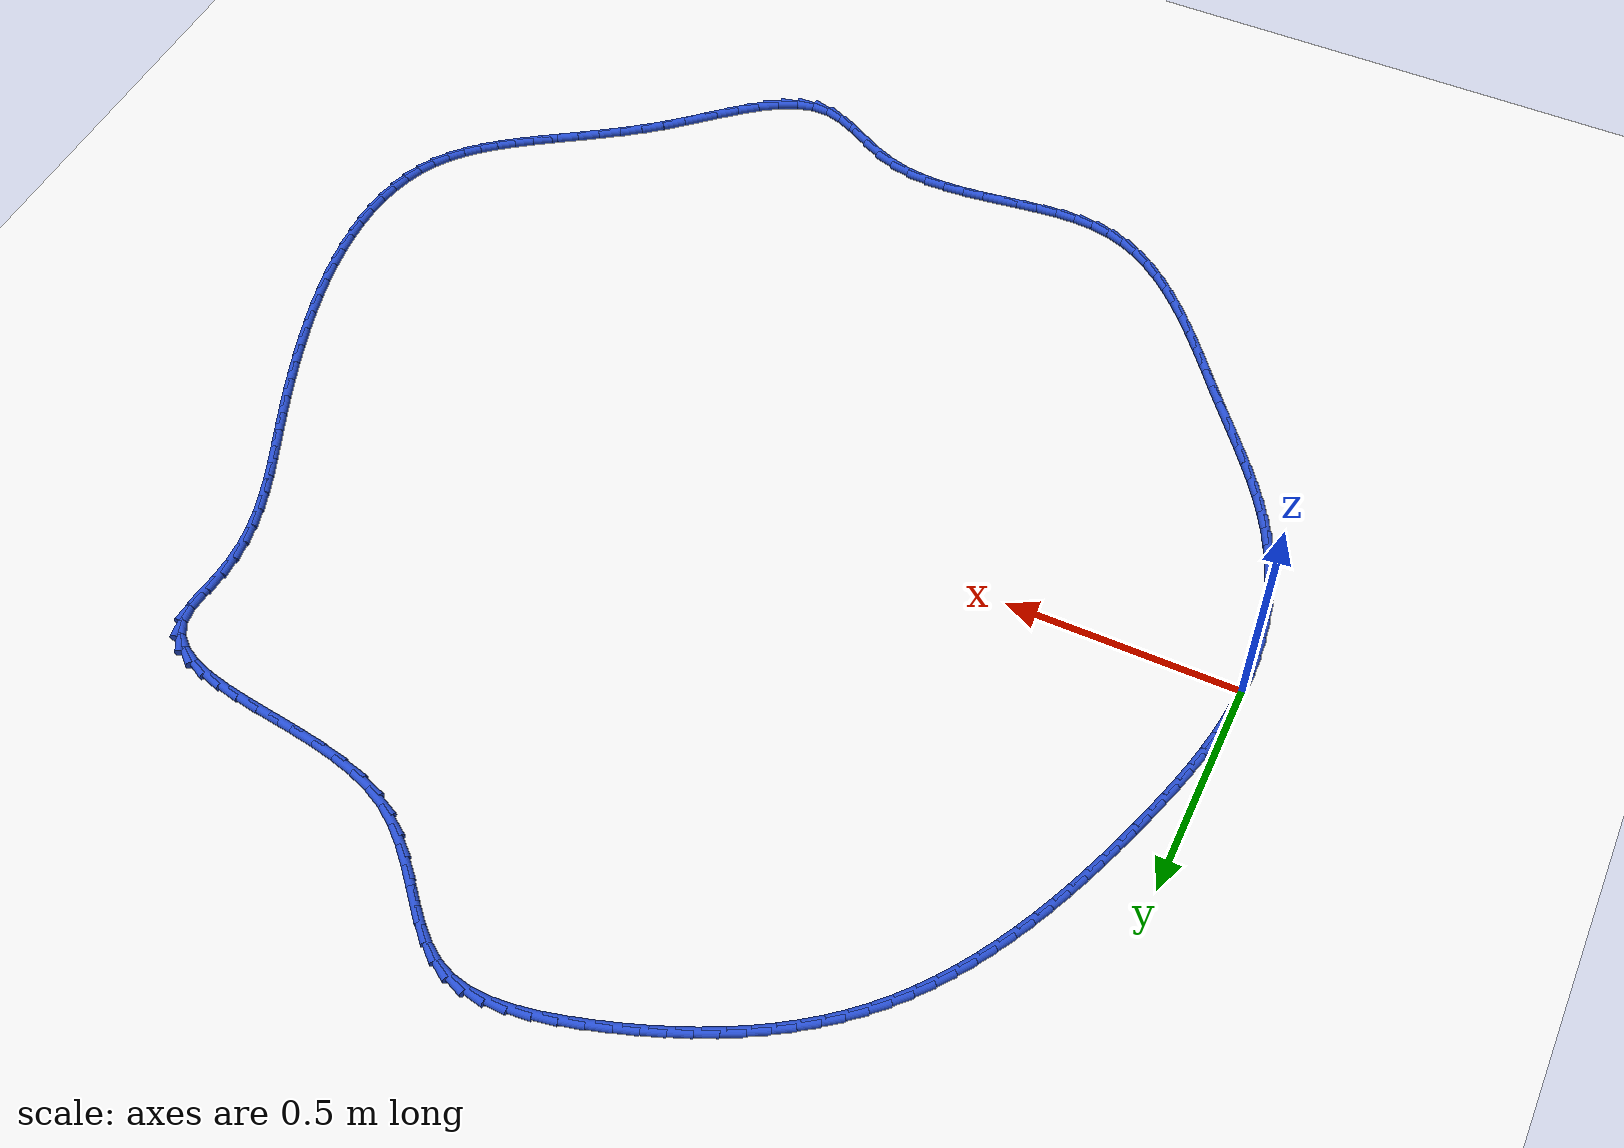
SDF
<sdf version="1.6">
 <world name="default">
  <light name="sun" type="directional">
   <pose>0 0 10 0 -0 0</pose>
   <diffuse>0.8 0.8 0.8 1</diffuse>
   <specular>0.2 0.2 0.2 1</specular>
   <attenuation>
    <range>1000</range>
    <constant>0.9</constant>
    <linear>0.01</linear>
    <quadratic>0.001</quadratic>
   </attenuation>
   <direction>-0.5 0.1 -0.9</direction>
  </light>
  <model name="ground_plane">
   <static>1</static>
   <link name="link">
    <collision name="collision">
     <geometry><plane><normal>0 0 1</normal><size>100 100</size></plane></geometry>
     <surface><friction><ode><mu>100</mu><mu2>50</mu2></ode></friction></surface>
    </collision>
    <visual name="visual">
     <cast_shadows>0</cast_shadows>
     <geometry><plane><normal>0 0 1</normal><size>100 100</size></plane></geometry>
     <material>
      <script><uri>file://media/materials/scripts/gazebo.material</uri><name>Gazebo/WhiteGlow</name></script>
     </material>
    </visual>
   </link>
  </model>
  <gravity>0 0 -9.8</gravity>
  <magnetic_field>6e-06 2.3e-05 -4.2e-05</magnetic_field>
  <atmosphere type="adiabatic"/>
  <physics name="default_physics" default="0" type="ode">
   <max_step_size>0.001</max_step_size>
   <real_time_factor>1</real_time_factor>
   <real_time_update_rate>1000</real_time_update_rate>
  </physics>
  <scene><ambient>0.4 0.4 0.4 1</ambient><background>0.7 0.7 0.7 1</background><shadows>1</shadows></scene>
  <spherical_coordinates>
   <surface_model>EARTH_WGS84</surface_model>
   <latitude_deg>0</latitude_deg>
   <longitude_deg>0</longitude_deg>
   <elevation>0</elevation>
   <heading_deg>0</heading_deg>
  </spherical_coordinates>
  <model name="line">
   <link name="link_0">
    <pose>-3.469446951953614e-18 -4.163336342344337e-17 0.01 0 1.57 1.5196897494440293</pose>
    <collision name="collision">
     <geometry><cylinder><radius>0.01</radius><length>0.08</length></cylinder></geometry>
    </collision>
    <visual name="visual">
     <material>
      <script><name>Gazebo/Blue</name><uri>file://media/materials/scripts/gazebo.material</uri></script>
     </material>
     <geometry><cylinder><radius>0.01</radius><length>0.08</length></cylinder></geometry>
    </visual>
   </link>
   <link name="link_1">
    <pose>0.002319896613140393 0.045353780587828935 0.01 0 1.57 1.4712630571093563</pose>
    <collision name="collision">
     <geometry><cylinder><radius>0.01</radius><length>0.08</length></cylinder></geometry>
    </collision>
    <visual name="visual">
     <material>
      <script><name>Gazebo/Blue</name><uri>file://media/materials/scripts/gazebo.material</uri></script>
     </material>
     <geometry><cylinder><radius>0.01</radius><length>0.08</length></cylinder></geometry>
    </visual>
   </link>
   <link name="link_2">
    <pose>0.006813461398471169 0.09035095523040214 0.01 0 1.57 1.4272608606687416</pose>
    <collision name="collision">
     <geometry><cylinder><radius>0.01</radius><length>0.08</length></cylinder></geometry>
    </collision>
    <visual name="visual">
     <material>
      <script><name>Gazebo/Blue</name><uri>file://media/materials/scripts/gazebo.material</uri></script>
     </material>
     <geometry><cylinder><radius>0.01</radius><length>0.08</length></cylinder></geometry>
    </visual>
   </link>
   <link name="link_3">
    <pose>0.013274008550931672 0.13505153418928748 0.01 0 1.57 1.3879731852438943</pose>
    <collision name="collision">
     <geometry><cylinder><radius>0.01</radius><length>0.08</length></cylinder></geometry>
    </collision>
    <visual name="visual">
     <material>
      <script><name>Gazebo/Blue</name><uri>file://media/materials/scripts/gazebo.material</uri></script>
     </material>
     <geometry><cylinder><radius>0.01</radius><length>0.08</length></cylinder></geometry>
    </visual>
   </link>
   <link name="link_4">
    <pose>0.02149485226546126 0.17951552772605295 0.01 0 1.57 1.3535736724575327</pose>
    <collision name="collision">
     <geometry><cylinder><radius>0.01</radius><length>0.08</length></cylinder></geometry>
    </collision>
    <visual name="visual">
     <material>
      <script><name>Gazebo/Blue</name><uri>file://media/materials/scripts/gazebo.material</uri></script>
     </material>
     <geometry><cylinder><radius>0.01</radius><length>0.08</length></cylinder></geometry>
    </visual>
   </link>
   <link name="link_5">
    <pose>0.03126930673699929 0.2238029461022665 0.01 0 1.57 1.3241421796897823</pose>
    <collision name="collision">
     <geometry><cylinder><radius>0.01</radius><length>0.08</length></cylinder></geometry>
    </collision>
    <visual name="visual">
     <material>
      <script><name>Gazebo/Blue</name><uri>file://media/materials/scripts/gazebo.material</uri></script>
     </material>
     <geometry><cylinder><radius>0.01</radius><length>0.08</length></cylinder></geometry>
    </visual>
   </link>
   <link name="link_6">
    <pose>0.04239068616048512 0.2679737995794961 0.01 0 1.57 1.2996885627056074</pose>
    <collision name="collision">
     <geometry><cylinder><radius>0.01</radius><length>0.08</length></cylinder></geometry>
    </collision>
    <visual name="visual">
     <material>
      <script><name>Gazebo/Blue</name><uri>file://media/materials/scripts/gazebo.material</uri></script>
     </material>
     <geometry><cylinder><radius>0.01</radius><length>0.08</length></cylinder></geometry>
    </visual>
   </link>
   <link name="link_7">
    <pose>0.05465230473085809 0.31208809841930957 0.01 0 1.57 1.2801747549238063</pose>
    <collision name="collision">
     <geometry><cylinder><radius>0.01</radius><length>0.08</length></cylinder></geometry>
    </collision>
    <visual name="visual">
     <material>
      <script><name>Gazebo/Blue</name><uri>file://media/materials/scripts/gazebo.material</uri></script>
     </material>
     <geometry><cylinder><radius>0.01</radius><length>0.08</length></cylinder></geometry>
    </visual>
   </link>
   <link name="link_8">
    <pose>0.06784747664305754 0.3562058528832749 0.01 0 1.57 1.2654561424635526</pose>
    <collision name="collision">
     <geometry><cylinder><radius>0.01</radius><length>0.08</length></cylinder></geometry>
    </collision>
    <visual name="visual">
     <material>
      <script><name>Gazebo/Blue</name><uri>file://media/materials/scripts/gazebo.material</uri></script>
     </material>
     <geometry><cylinder><radius>0.01</radius><length>0.08</length></cylinder></geometry>
    </visual>
   </link>
   <link name="link_9">
    <pose>0.0817725992260276 0.40038493824453897 0.01 0 1.57 1.2524589045999632</pose>
    <collision name="collision">
     <geometry><cylinder><radius>0.01</radius><length>0.08</length></cylinder></geometry>
    </collision>
    <visual name="visual">
     <material>
      <script><name>Gazebo/Blue</name><uri>file://media/materials/scripts/gazebo.material</uri></script>
     </material>
     <geometry><cylinder><radius>0.01</radius><length>0.08</length></cylinder></geometry>
    </visual>
   </link>
   <link name="link_10">
    <pose>0.09634361159663021 0.4446004502627239 0.01 0 1.57 1.237232875810625</pose>
    <collision name="collision">
     <geometry><cylinder><radius>0.01</radius><length>0.08</length></cylinder></geometry>
    </collision>
    <visual name="visual">
     <material>
      <script><name>Gazebo/Blue</name><uri>file://media/materials/scripts/gazebo.material</uri></script>
     </material>
     <geometry><cylinder><radius>0.01</radius><length>0.08</length></cylinder></geometry>
    </visual>
   </link>
   <link name="link_11">
    <pose>0.1116315598684818 0.4887200772212944 0.01 0 1.57 1.219444315659839</pose>
    <collision name="collision">
     <geometry><cylinder><radius>0.01</radius><length>0.08</length></cylinder></geometry>
    </collision>
    <visual name="visual">
     <material>
      <script><name>Gazebo/Blue</name><uri>file://media/materials/scripts/gazebo.material</uri></script>
     </material>
     <geometry><cylinder><radius>0.01</radius><length>0.08</length></cylinder></geometry>
    </visual>
   </link>
   <link name="link_12">
    <pose>0.127717837928115 0.5326043418457709 0.01 0 1.57 1.1989935987830704</pose>
    <collision name="collision">
     <geometry><cylinder><radius>0.01</radius><length>0.08</length></cylinder></geometry>
    </collision>
    <visual name="visual">
     <material>
      <script><name>Gazebo/Blue</name><uri>file://media/materials/scripts/gazebo.material</uri></script>
     </material>
     <geometry><cylinder><radius>0.01</radius><length>0.08</length></cylinder></geometry>
    </visual>
   </link>
   <link name="link_13">
    <pose>0.14468383966206252 0.576113766861674 0.01 0 1.57 1.1757576896094266</pose>
    <collision name="collision">
     <geometry><cylinder><radius>0.01</radius><length>0.08</length></cylinder></geometry>
    </collision>
    <visual name="visual">
     <material>
      <script><name>Gazebo/Blue</name><uri>file://media/materials/scripts/gazebo.material</uri></script>
     </material>
     <geometry><cylinder><radius>0.01</radius><length>0.08</length></cylinder></geometry>
    </visual>
   </link>
   <link name="link_14">
    <pose>0.16261095895685698 0.6191088749945239 0.01 0 1.57 1.1495926434329429</pose>
    <collision name="collision">
     <geometry><cylinder><radius>0.01</radius><length>0.08</length></cylinder></geometry>
    </collision>
    <visual name="visual">
     <material>
      <script><name>Gazebo/Blue</name><uri>file://media/materials/scripts/gazebo.material</uri></script>
     </material>
     <geometry><cylinder><radius>0.01</radius><length>0.08</length></cylinder></geometry>
    </visual>
   </link>
   <link name="link_15">
    <pose>0.1815805896990312 0.6614501889698416 0.01 0 1.57 1.1203369771391016</pose>
    <collision name="collision">
     <geometry><cylinder><radius>0.01</radius><length>0.08</length></cylinder></geometry>
    </collision>
    <visual name="visual">
     <material>
      <script><name>Gazebo/Blue</name><uri>file://media/materials/scripts/gazebo.material</uri></script>
     </material>
     <geometry><cylinder><radius>0.01</radius><length>0.08</length></cylinder></geometry>
    </visual>
   </link>
   <link name="link_16">
    <pose>0.20167412577511776 0.7029982315131472 0.01 0 1.57 1.0878164156162171</pose>
    <collision name="collision">
     <geometry><cylinder><radius>0.01</radius><length>0.08</length></cylinder></geometry>
    </collision>
    <visual name="visual">
     <material>
      <script><name>Gazebo/Blue</name><uri>file://media/materials/scripts/gazebo.material</uri></script>
     </material>
     <geometry><cylinder><radius>0.01</radius><length>0.08</length></cylinder></geometry>
    </visual>
   </link>
   <link name="link_17">
    <pose>0.22297296107164946 0.7436135253499614 0.01 0 1.57 1.0518506044389189</pose>
    <collision name="collision">
     <geometry><cylinder><radius>0.01</radius><length>0.08</length></cylinder></geometry>
    </collision>
    <visual name="visual">
     <material>
      <script><name>Gazebo/Blue</name><uri>file://media/materials/scripts/gazebo.material</uri></script>
     </material>
     <geometry><cylinder><radius>0.01</radius><length>0.08</length></cylinder></geometry>
    </visual>
   </link>
   <link name="link_18">
    <pose>0.24555848947515885 0.7831565932058046 0.01 0 1.57 1.0122624396479463</pose>
    <collision name="collision">
     <geometry><cylinder><radius>0.01</radius><length>0.08</length></cylinder></geometry>
    </collision>
    <visual name="visual">
     <material>
      <script><name>Gazebo/Blue</name><uri>file://media/materials/scripts/gazebo.material</uri></script>
     </material>
     <geometry><cylinder><radius>0.01</radius><length>0.08</length></cylinder></geometry>
    </visual>
   </link>
   <link name="link_19">
    <pose>0.2695121048721787 0.8214879578061972 0.01 0 1.57 0.9688906565132857</pose>
    <collision name="collision">
     <geometry><cylinder><radius>0.01</radius><length>0.08</length></cylinder></geometry>
    </collision>
    <visual name="visual">
     <material>
      <script><name>Gazebo/Blue</name><uri>file://media/materials/scripts/gazebo.material</uri></script>
     </material>
     <geometry><cylinder><radius>0.01</radius><length>0.08</length></cylinder></geometry>
    </visual>
   </link>
   <link name="link_20">
    <pose>0.29491520114924175 0.8584681418766602 0.01 0 1.57 0.9216061732869267</pose>
    <collision name="collision">
     <geometry><cylinder><radius>0.01</radius><length>0.08</length></cylinder></geometry>
    </collision>
    <visual name="visual">
     <material>
      <script><name>Gazebo/Blue</name><uri>file://media/materials/scripts/gazebo.material</uri></script>
     </material>
     <geometry><cylinder><radius>0.01</radius><length>0.08</length></cylinder></geometry>
    </visual>
   </link>
   <link name="link_21">
    <pose>0.3218491721928806 0.8939576681427135 0.01 0 1.57 0.8703323150895607</pose>
    <collision name="collision">
     <geometry><cylinder><radius>0.01</radius><length>0.08</length></cylinder></geometry>
    </collision>
    <visual name="visual">
     <material>
      <script><name>Gazebo/Blue</name><uri>file://media/materials/scripts/gazebo.material</uri></script>
     </material>
     <geometry><cylinder><radius>0.01</radius><length>0.08</length></cylinder></geometry>
    </visual>
   </link>
   <link name="link_22">
    <pose>0.350395411889628 0.9278170593298778 0.01 0 1.57 0.8150801811149491</pose>
    <collision name="collision">
     <geometry><cylinder><radius>0.01</radius><length>0.08</length></cylinder></geometry>
    </collision>
    <visual name="visual">
     <material>
      <script><name>Gazebo/Blue</name><uri>file://media/materials/scripts/gazebo.material</uri></script>
     </material>
     <geometry><cylinder><radius>0.01</radius><length>0.08</length></cylinder></geometry>
    </visual>
   </link>
   <link name="link_23">
    <pose>0.38063501984642284 0.9599072860546687 0.01 0 1.57 0.7576464526183997</pose>
    <collision name="collision">
     <geometry><cylinder><radius>0.01</radius><length>0.08</length></cylinder></geometry>
    </collision>
    <visual name="visual">
     <material>
      <script><name>Gazebo/Blue</name><uri>file://media/materials/scripts/gazebo.material</uri></script>
     </material>
     <geometry><cylinder><radius>0.01</radius><length>0.08</length></cylinder></geometry>
    </visual>
   </link>
   <link name="link_24">
    <pose>0.412607482400008 0.990152653970726 0.01 0 1.57 0.7017560576542322</pose>
    <collision name="collision">
     <geometry><cylinder><radius>0.01</radius><length>0.08</length></cylinder></geometry>
    </collision>
    <visual name="visual">
     <material>
      <script><name>Gazebo/Blue</name><uri>file://media/materials/scripts/gazebo.material</uri></script>
     </material>
     <geometry><cylinder><radius>0.01</radius><length>0.08</length></cylinder></geometry>
    </visual>
   </link>
   <link name="link_25">
    <pose>0.4462680165875392 1.0186057258764094 0.01 0 1.57 0.6481740545595359</pose>
    <collision name="collision">
     <geometry><cylinder><radius>0.01</radius><length>0.08</length></cylinder></geometry>
    </collision>
    <visual name="visual">
     <material>
      <script><name>Gazebo/Blue</name><uri>file://media/materials/scripts/gazebo.material</uri></script>
     </material>
     <geometry><cylinder><radius>0.01</radius><length>0.08</length></cylinder></geometry>
    </visual>
   </link>
   <link name="link_26">
    <pose>0.4815616578927056 1.045334560806345 0.01 0 1.57 0.5971737637278237</pose>
    <collision name="collision">
     <geometry><cylinder><radius>0.01</radius><length>0.08</length></cylinder></geometry>
    </collision>
    <visual name="visual">
     <material>
      <script><name>Gazebo/Blue</name><uri>file://media/materials/scripts/gazebo.material</uri></script>
     </material>
     <geometry><cylinder><radius>0.01</radius><length>0.08</length></cylinder></geometry>
    </visual>
   </link>
   <link name="link_27">
    <pose>0.5184334417991961 1.0704072177951593 0.01 0 1.57 0.5489465880118373</pose>
    <collision name="collision">
     <geometry><cylinder><radius>0.01</radius><length>0.08</length></cylinder></geometry>
    </collision>
    <visual name="visual">
     <material>
      <script><name>Gazebo/Blue</name><uri>file://media/materials/scripts/gazebo.material</uri></script>
     </material>
     <geometry><cylinder><radius>0.01</radius><length>0.08</length></cylinder></geometry>
    </visual>
   </link>
   <link name="link_28">
    <pose>0.5568284037907001 1.0938917558774792 0.01 0 1.57 0.5036081100700573</pose>
    <collision name="collision">
     <geometry><cylinder><radius>0.01</radius><length>0.08</length></cylinder></geometry>
    </collision>
    <visual name="visual">
     <material>
      <script><name>Gazebo/Blue</name><uri>file://media/materials/scripts/gazebo.material</uri></script>
     </material>
     <geometry><cylinder><radius>0.01</radius><length>0.08</length></cylinder></geometry>
    </visual>
   </link>
   <link name="link_29">
    <pose>0.5966915793509059 1.1158562340879303 0.01 0 1.57 0.4612077063151371</pose>
    <collision name="collision">
     <geometry><cylinder><radius>0.01</radius><length>0.08</length></cylinder></geometry>
    </collision>
    <visual name="visual">
     <material>
      <script><name>Gazebo/Blue</name><uri>file://media/materials/scripts/gazebo.material</uri></script>
     </material>
     <geometry><cylinder><radius>0.01</radius><length>0.08</length></cylinder></geometry>
    </visual>
   </link>
   <link name="link_30">
    <pose>0.6379680039635028 1.13636871146114 0.01 0 1.57 0.42173993936755605</pose>
    <collision name="collision">
     <geometry><cylinder><radius>0.01</radius><length>0.08</length></cylinder></geometry>
    </collision>
    <visual name="visual">
     <material>
      <script><name>Gazebo/Blue</name><uri>file://media/materials/scripts/gazebo.material</uri></script>
     </material>
     <geometry><cylinder><radius>0.01</radius><length>0.08</length></cylinder></geometry>
    </visual>
   </link>
   <link name="link_31">
    <pose>0.6806027131121801 1.1554972470317342 0.01 0 1.57 0.3851562998369419</pose>
    <collision name="collision">
     <geometry><cylinder><radius>0.01</radius><length>0.08</length></cylinder></geometry>
    </collision>
    <visual name="visual">
     <material>
      <script><name>Gazebo/Blue</name><uri>file://media/materials/scripts/gazebo.material</uri></script>
     </material>
     <geometry><cylinder><radius>0.01</radius><length>0.08</length></cylinder></geometry>
    </visual>
   </link>
   <link name="link_32">
    <pose>0.7245407422806268 1.1733098998343396 0.01 0 1.57 0.3513762811967945</pose>
    <collision name="collision">
     <geometry><cylinder><radius>0.01</radius><length>0.08</length></cylinder></geometry>
    </collision>
    <visual name="visual">
     <material>
      <script><name>Gazebo/Blue</name><uri>file://media/materials/scripts/gazebo.material</uri></script>
     </material>
     <geometry><cylinder><radius>0.01</radius><length>0.08</length></cylinder></geometry>
    </visual>
   </link>
   <link name="link_33">
    <pose>0.7697271269525315 1.1898747289035827 0.01 0 1.57 0.3202971706648542</pose>
    <collision name="collision">
     <geometry><cylinder><radius>0.01</radius><length>0.08</length></cylinder></geometry>
    </collision>
    <visual name="visual">
     <material>
      <script><name>Gazebo/Blue</name><uri>file://media/materials/scripts/gazebo.material</uri></script>
     </material>
     <geometry><cylinder><radius>0.01</radius><length>0.08</length></cylinder></geometry>
    </visual>
   </link>
   <link name="link_34">
    <pose>0.8161069023848896 1.2052597929166446 0.01 0 1.57 0.28849324613542543</pose>
    <collision name="collision">
     <geometry><cylinder><radius>0.01</radius><length>0.08</length></cylinder></geometry>
    </collision>
    <visual name="visual">
     <material>
      <script><name>Gazebo/Blue</name><uri>file://media/materials/scripts/gazebo.material</uri></script>
     </material>
     <geometry><cylinder><radius>0.01</radius><length>0.08</length></cylinder></geometry>
    </visual>
   </link>
   <link name="link_35">
    <pose>0.8634913087338368 1.2193221860201986 0.01 0 1.57 0.24225145650850913</pose>
    <collision name="collision">
     <geometry><cylinder><radius>0.01</radius><length>0.08</length></cylinder></geometry>
    </collision>
    <visual name="visual">
     <material>
      <script><name>Gazebo/Blue</name><uri>file://media/materials/scripts/gazebo.material</uri></script>
     </material>
     <geometry><cylinder><radius>0.01</radius><length>0.08</length></cylinder></geometry>
    </visual>
   </link>
   <link name="link_36">
    <pose>0.9111754275511804 1.2311051373020987 0.01 0 1.57 0.17527124483362222</pose>
    <collision name="collision">
     <geometry><cylinder><radius>0.01</radius><length>0.08</length></cylinder></geometry>
    </collision>
    <visual name="visual">
     <material>
      <script><name>Gazebo/Blue</name><uri>file://media/materials/scripts/gazebo.material</uri></script>
     </material>
     <geometry><cylinder><radius>0.01</radius><length>0.08</length></cylinder></geometry>
    </visual>
   </link>
   <link name="link_37">
    <pose>0.9583298883349487 1.2394556431860153 0.01 0 1.57 0.08203019321381604</pose>
    <collision name="collision">
     <geometry><cylinder><radius>0.01</radius><length>0.08</length></cylinder></geometry>
    </collision>
    <visual name="visual">
     <material>
      <script><name>Gazebo/Blue</name><uri>file://media/materials/scripts/gazebo.material</uri></script>
     </material>
     <geometry><cylinder><radius>0.01</radius><length>0.08</length></cylinder></geometry>
    </visual>
   </link>
   <link name="link_38">
    <pose>1.0041253205831697 1.243220700095619 0.01 0 1.57 -0.04522321338786801</pose>
    <collision name="collision">
     <geometry><cylinder><radius>0.01</radius><length>0.08</length></cylinder></geometry>
    </collision>
    <visual name="visual">
     <material>
      <script><name>Gazebo/Blue</name><uri>file://media/materials/scripts/gazebo.material</uri></script>
     </material>
     <geometry><cylinder><radius>0.01</radius><length>0.08</length></cylinder></geometry>
    </visual>
   </link>
   <link name="link_39">
    <pose>1.0477323537938728 1.2412473044545818 0.01 0 1.57 -0.21502734061907003</pose>
    <collision name="collision">
     <geometry><cylinder><radius>0.01</radius><length>0.08</length></cylinder></geometry>
    </collision>
    <visual name="visual">
     <material>
      <script><name>Gazebo/Blue</name><uri>file://media/materials/scripts/gazebo.material</uri></script>
     </material>
     <geometry><cylinder><radius>0.01</radius><length>0.08</length></cylinder></geometry>
    </visual>
   </link>
   <link name="link_40">
    <pose>1.0883216174650845 1.232382452686573 0.01 0 1.57 -0.4235309624702591</pose>
    <collision name="collision">
     <geometry><cylinder><radius>0.01</radius><length>0.08</length></cylinder></geometry>
    </collision>
    <visual name="visual">
     <material>
      <script><name>Gazebo/Blue</name><uri>file://media/materials/scripts/gazebo.material</uri></script>
     </material>
     <geometry><cylinder><radius>0.01</radius><length>0.08</length></cylinder></geometry>
    </visual>
   </link>
   <link name="link_41">
    <pose>1.1252436023418861 1.2157374908021974 0.01 0 1.57 -0.6091120513835694</pose>
    <collision name="collision">
     <geometry><cylinder><radius>0.01</radius><length>0.08</length></cylinder></geometry>
    </collision>
    <visual name="visual">
     <material>
      <script><name>Gazebo/Blue</name><uri>file://media/materials/scripts/gazebo.material</uri></script>
     </material>
     <geometry><cylinder><radius>0.01</radius><length>0.08</length></cylinder></geometry>
    </visual>
   </link>
   <link name="link_42">
    <pose>1.1590338494181325 1.1921654826578747 0.01 0 1.57 -0.7403511831538201</pose>
    <collision name="collision">
     <geometry><cylinder><radius>0.01</radius><length>0.08</length></cylinder></geometry>
    </collision>
    <visual name="visual">
     <material>
      <script><name>Gazebo/Blue</name><uri>file://media/materials/scripts/gazebo.material</uri></script>
     </material>
     <geometry><cylinder><radius>0.01</radius><length>0.08</length></cylinder></geometry>
    </visual>
   </link>
   <link name="link_43">
    <pose>1.1907074242692988 1.1632242694156079 0.01 0 1.57 -0.8197676711153987</pose>
    <collision name="collision">
     <geometry><cylinder><radius>0.01</radius><length>0.08</length></cylinder></geometry>
    </collision>
    <visual name="visual">
     <material>
      <script><name>Gazebo/Blue</name><uri>file://media/materials/scripts/gazebo.material</uri></script>
     </material>
     <geometry><cylinder><radius>0.01</radius><length>0.08</length></cylinder></geometry>
    </visual>
   </link>
   <link name="link_44">
    <pose>1.2212807448318435 1.130473679858819 0.01 0 1.57 -0.854165402444591</pose>
    <collision name="collision">
     <geometry><cylinder><radius>0.01</radius><length>0.08</length></cylinder></geometry>
    </collision>
    <visual name="visual">
     <material>
      <script><name>Gazebo/Blue</name><uri>file://media/materials/scripts/gazebo.material</uri></script>
     </material>
     <geometry><cylinder><radius>0.01</radius><length>0.08</length></cylinder></geometry>
    </visual>
   </link>
   <link name="link_45">
    <pose>1.2517702290422241 1.0954735427709308 0.01 0 1.57 -0.8489047794096215</pose>
    <collision name="collision">
     <geometry><cylinder><radius>0.01</radius><length>0.08</length></cylinder></geometry>
    </collision>
    <visual name="visual">
     <material>
      <script><name>Gazebo/Blue</name><uri>file://media/materials/scripts/gazebo.material</uri></script>
     </material>
     <geometry><cylinder><radius>0.01</radius><length>0.08</length></cylinder></geometry>
    </visual>
   </link>
   <link name="link_46">
    <pose>1.2831922948368992 1.0597836869353658 0.01 0 1.57 -0.8066394798700118</pose>
    <collision name="collision">
     <geometry><cylinder><radius>0.01</radius><length>0.08</length></cylinder></geometry>
    </collision>
    <visual name="visual">
     <material>
      <script><name>Gazebo/Blue</name><uri>file://media/materials/scripts/gazebo.material</uri></script>
     </material>
     <geometry><cylinder><radius>0.01</radius><length>0.08</length></cylinder></geometry>
    </visual>
   </link>
   <link name="link_47">
    <pose>1.3165633601523261 1.024963941135547 0.01 0 1.57 -0.7280351660212289</pose>
    <collision name="collision">
     <geometry><cylinder><radius>0.01</radius><length>0.08</length></cylinder></geometry>
    </collision>
    <visual name="visual">
     <material>
      <script><name>Gazebo/Blue</name><uri>file://media/materials/scripts/gazebo.material</uri></script>
     </material>
     <geometry><cylinder><radius>0.01</radius><length>0.08</length></cylinder></geometry>
    </visual>
   </link>
   <link name="link_48">
    <pose>1.352899842924964 0.9925741341548966 0.01 0 1.57 -0.6136698351476273</pose>
    <collision name="collision">
     <geometry><cylinder><radius>0.01</radius><length>0.08</length></cylinder></geometry>
    </collision>
    <visual name="visual">
     <material>
      <script><name>Gazebo/Blue</name><uri>file://media/materials/scripts/gazebo.material</uri></script>
     </material>
     <geometry><cylinder><radius>0.01</radius><length>0.08</length></cylinder></geometry>
    </visual>
   </link>
   <link name="link_49">
    <pose>1.3932181610912697 0.9641740947768377 0.01 0 1.57 -0.47128126982619345</pose>
    <collision name="collision">
     <geometry><cylinder><radius>0.01</radius><length>0.08</length></cylinder></geometry>
    </collision>
    <visual name="visual">
     <material>
      <script><name>Gazebo/Blue</name><uri>file://media/materials/scripts/gazebo.material</uri></script>
     </material>
     <geometry><cylinder><radius>0.01</radius><length>0.08</length></cylinder></geometry>
    </visual>
   </link>
   <link name="link_50">
    <pose>1.43839035071041 0.9411553035657774 0.01 0 1.57 -0.3453012266294161</pose>
    <collision name="collision">
     <geometry><cylinder><radius>0.01</radius><length>0.08</length></cylinder></geometry>
    </collision>
    <visual name="visual">
     <material>
      <script><name>Gazebo/Blue</name><uri>file://media/materials/scripts/gazebo.material</uri></script>
     </material>
     <geometry><cylinder><radius>0.01</radius><length>0.08</length></cylinder></geometry>
    </visual>
   </link>
   <link name="link_51">
    <pose>1.4879365290332625 0.9233329135864541 0.01 0 1.57 -0.25382891757842035</pose>
    <collision name="collision">
     <geometry><cylinder><radius>0.01</radius><length>0.08</length></cylinder></geometry>
    </collision>
    <visual name="visual">
     <material>
      <script><name>Gazebo/Blue</name><uri>file://media/materials/scripts/gazebo.material</uri></script>
     </material>
     <geometry><cylinder><radius>0.01</radius><length>0.08</length></cylinder></geometry>
    </visual>
   </link>
   <link name="link_52">
    <pose>1.540638164307854 0.9096608185375467 0.01 0 1.57 -0.19123548136641294</pose>
    <collision name="collision">
     <geometry><cylinder><radius>0.01</radius><length>0.08</length></cylinder></geometry>
    </collision>
    <visual name="visual">
     <material>
      <script><name>Gazebo/Blue</name><uri>file://media/materials/scripts/gazebo.material</uri></script>
     </material>
     <geometry><cylinder><radius>0.01</radius><length>0.08</length></cylinder></geometry>
    </visual>
   </link>
   <link name="link_53">
    <pose>1.5952692291257269 0.899084172236776 0.01 0 1.57 -0.15305620839267559</pose>
    <collision name="collision">
     <geometry><cylinder><radius>0.01</radius><length>0.08</length></cylinder></geometry>
    </collision>
    <visual name="visual">
     <material>
      <script><name>Gazebo/Blue</name><uri>file://media/materials/scripts/gazebo.material</uri></script>
     </material>
     <geometry><cylinder><radius>0.01</radius><length>0.08</length></cylinder></geometry>
    </visual>
   </link>
   <link name="link_54">
    <pose>1.6506036960784234 0.8905481285018645 0.01 0 1.57 -0.13688773041719374</pose>
    <collision name="collision">
     <geometry><cylinder><radius>0.01</radius><length>0.08</length></cylinder></geometry>
    </collision>
    <visual name="visual">
     <material>
      <script><name>Gazebo/Blue</name><uri>file://media/materials/scripts/gazebo.material</uri></script>
     </material>
     <geometry><cylinder><radius>0.01</radius><length>0.08</length></cylinder></geometry>
    </visual>
   </link>
   <link name="link_55">
    <pose>1.705415537757486 0.8829978411505341 0.01 0 1.57 -0.14261580568403587</pose>
    <collision name="collision">
     <geometry><cylinder><radius>0.01</radius><length>0.08</length></cylinder></geometry>
    </collision>
    <visual name="visual">
     <material>
      <script><name>Gazebo/Blue</name><uri>file://media/materials/scripts/gazebo.material</uri></script>
     </material>
     <geometry><cylinder><radius>0.01</radius><length>0.08</length></cylinder></geometry>
    </visual>
   </link>
   <link name="link_56">
    <pose>1.758478726754457 0.8753784640005066 0.01 0 1.57 -0.17281605520546106</pose>
    <collision name="collision">
     <geometry><cylinder><radius>0.01</radius><length>0.08</length></cylinder></geometry>
    </collision>
    <visual name="visual">
     <material>
      <script><name>Gazebo/Blue</name><uri>file://media/materials/scripts/gazebo.material</uri></script>
     </material>
     <geometry><cylinder><radius>0.01</radius><length>0.08</length></cylinder></geometry>
    </visual>
   </link>
   <link name="link_57">
    <pose>1.8085672356608784 0.8666351508695038 0.01 0 1.57 -0.23366951964585844</pose>
    <collision name="collision">
     <geometry><cylinder><radius>0.01</radius><length>0.08</length></cylinder></geometry>
    </collision>
    <visual name="visual">
     <material>
      <script><name>Gazebo/Blue</name><uri>file://media/materials/scripts/gazebo.material</uri></script>
     </material>
     <geometry><cylinder><radius>0.01</radius><length>0.08</length></cylinder></geometry>
    </visual>
   </link>
   <link name="link_58">
    <pose>1.8544550370682924 0.8557130555752475 0.01 0 1.57 -0.33655042074562525</pose>
    <collision name="collision">
     <geometry><cylinder><radius>0.01</radius><length>0.08</length></cylinder></geometry>
    </collision>
    <visual name="visual">
     <material>
      <script><name>Gazebo/Blue</name><uri>file://media/materials/scripts/gazebo.material</uri></script>
     </material>
     <geometry><cylinder><radius>0.01</radius><length>0.08</length></cylinder></geometry>
    </visual>
   </link>
   <link name="link_59">
    <pose>1.89491610356824 0.8415573319354597 0.01 0 1.57 -0.49942205946277485</pose>
    <collision name="collision">
     <geometry><cylinder><radius>0.01</radius><length>0.08</length></cylinder></geometry>
    </collision>
    <visual name="visual">
     <material>
      <script><name>Gazebo/Blue</name><uri>file://media/materials/scripts/gazebo.material</uri></script>
     </material>
     <geometry><cylinder><radius>0.01</radius><length>0.08</length></cylinder></geometry>
    </visual>
   </link>
   <link name="link_60">
    <pose>1.9287244077522654 0.8231131337678623 0.01 0 1.57 -0.7423410543482986</pose>
    <collision name="collision">
     <geometry><cylinder><radius>0.01</radius><length>0.08</length></cylinder></geometry>
    </collision>
    <visual name="visual">
     <material>
      <script><name>Gazebo/Blue</name><uri>file://media/materials/scripts/gazebo.material</uri></script>
     </material>
     <geometry><cylinder><radius>0.01</radius><length>0.08</length></cylinder></geometry>
    </visual>
   </link>
   <link name="link_61">
    <pose>1.9546539222119088 0.7993256148901767 0.01 0 1.57 -1.0623098117566379</pose>
    <collision name="collision">
     <geometry><cylinder><radius>0.01</radius><length>0.08</length></cylinder></geometry>
    </collision>
    <visual name="visual">
     <material>
      <script><name>Gazebo/Blue</name><uri>file://media/materials/scripts/gazebo.material</uri></script>
     </material>
     <geometry><cylinder><radius>0.01</radius><length>0.08</length></cylinder></geometry>
    </visual>
   </link>
   <link name="link_62">
    <pose>1.9714786195387142 0.7691399291201259 0.01 0 1.57 -1.3993604400209143</pose>
    <collision name="collision">
     <geometry><cylinder><radius>0.01</radius><length>0.08</length></cylinder></geometry>
    </collision>
    <visual name="visual">
     <material>
      <script><name>Gazebo/Blue</name><uri>file://media/materials/scripts/gazebo.material</uri></script>
     </material>
     <geometry><cylinder><radius>0.01</radius><length>0.08</length></cylinder></geometry>
    </visual>
   </link>
   <link name="link_63">
    <pose>1.9779929084815504 0.7315145241914516 0.01 0 1.57 1.5167620097109134</pose>
    <collision name="collision">
     <geometry><cylinder><radius>0.01</radius><length>0.08</length></cylinder></geometry>
    </collision>
    <visual name="visual">
     <material>
      <script><name>Gazebo/Blue</name><uri>file://media/materials/scripts/gazebo.material</uri></script>
     </material>
     <geometry><cylinder><radius>0.01</radius><length>0.08</length></cylinder></geometry>
    </visual>
   </link>
   <link name="link_64">
    <pose>1.9755905956606663 0.687098781042876 0.01 0 1.57 1.4693591732198337</pose>
    <collision name="collision">
     <geometry><cylinder><radius>0.01</radius><length>0.08</length></cylinder></geometry>
    </collision>
    <visual name="visual">
     <material>
      <script><name>Gazebo/Blue</name><uri>file://media/materials/scripts/gazebo.material</uri></script>
     </material>
     <geometry><cylinder><radius>0.01</radius><length>0.08</length></cylinder></geometry>
    </visual>
   </link>
   <link name="link_65">
    <pose>1.9707834842706506 0.6398713863903556 0.01 0 1.57 1.5431513272881845</pose>
    <collision name="collision">
     <geometry><cylinder><radius>0.01</radius><length>0.08</length></cylinder></geometry>
    </collision>
    <visual name="visual">
     <material>
      <script><name>Gazebo/Blue</name><uri>file://media/materials/scripts/gazebo.material</uri></script>
     </material>
     <geometry><cylinder><radius>0.01</radius><length>0.08</length></cylinder></geometry>
    </visual>
   </link>
   <link name="link_66">
    <pose>1.9695006009935125 0.5934775911084603 0.01 0 1.57 -1.5024310687218616</pose>
    <collision name="collision">
     <geometry><cylinder><radius>0.01</radius><length>0.08</length></cylinder></geometry>
    </collision>
    <visual name="visual">
     <material>
      <script><name>Gazebo/Blue</name><uri>file://media/materials/scripts/gazebo.material</uri></script>
     </material>
     <geometry><cylinder><radius>0.01</radius><length>0.08</length></cylinder></geometry>
    </visual>
   </link>
   <link name="link_67">
    <pose>1.972583721075551 0.5484501112569047 0.01 0 1.57 -1.4146633289215687</pose>
    <collision name="collision">
     <geometry><cylinder><radius>0.01</radius><length>0.08</length></cylinder></geometry>
    </collision>
    <visual name="visual">
     <material>
      <script><name>Gazebo/Blue</name><uri>file://media/materials/scripts/gazebo.material</uri></script>
     </material>
     <geometry><cylinder><radius>0.01</radius><length>0.08</length></cylinder></geometry>
    </visual>
   </link>
   <link name="link_68">
    <pose>1.9795046904083984 0.5044834985419824 0.01 0 1.57 -1.3383180069471894</pose>
    <collision name="collision">
     <geometry><cylinder><radius>0.01</radius><length>0.08</length></cylinder></geometry>
    </collision>
    <visual name="visual">
     <material>
      <script><name>Gazebo/Blue</name><uri>file://media/materials/scripts/gazebo.material</uri></script>
     </material>
     <geometry><cylinder><radius>0.01</radius><length>0.08</length></cylinder></geometry>
    </visual>
   </link>
   <link name="link_69">
    <pose>1.9897353354917005 0.46127229280538184 0.01 0 1.57 -1.2754014826015665</pose>
    <collision name="collision">
     <geometry><cylinder><radius>0.01</radius><length>0.08</length></cylinder></geometry>
    </collision>
    <visual name="visual">
     <material>
      <script><name>Gazebo/Blue</name><uri>file://media/materials/scripts/gazebo.material</uri></script>
     </material>
     <geometry><cylinder><radius>0.01</radius><length>0.08</length></cylinder></geometry>
    </visual>
   </link>
   <link name="link_70">
    <pose>2.0027474828251006 0.4185110338887897 0.01 0 1.57 -1.2268320605868643</pose>
    <collision name="collision">
     <geometry><cylinder><radius>0.01</radius><length>0.08</length></cylinder></geometry>
    </collision>
    <visual name="visual">
     <material>
      <script><name>Gazebo/Blue</name><uri>file://media/materials/scripts/gazebo.material</uri></script>
     </material>
     <geometry><cylinder><radius>0.01</radius><length>0.08</length></cylinder></geometry>
    </visual>
   </link>
   <link name="link_71">
    <pose>2.0180129589082445 0.37589426163389306 0.01 0 1.57 -1.192719988314084</pose>
    <collision name="collision">
     <geometry><cylinder><radius>0.01</radius><length>0.08</length></cylinder></geometry>
    </collision>
    <visual name="visual">
     <material>
      <script><name>Gazebo/Blue</name><uri>file://media/materials/scripts/gazebo.material</uri></script>
     </material>
     <geometry><cylinder><radius>0.01</radius><length>0.08</length></cylinder></geometry>
    </visual>
   </link>
   <link name="link_72">
    <pose>2.035003590240775 0.33311651588238006 0.01 0 1.57 -1.1726758772768295</pose>
    <collision name="collision">
     <geometry><cylinder><radius>0.01</radius><length>0.08</length></cylinder></geometry>
    </collision>
    <visual name="visual">
     <material>
      <script><name>Gazebo/Blue</name><uri>file://media/materials/scripts/gazebo.material</uri></script>
     </material>
     <geometry><cylinder><radius>0.01</radius><length>0.08</length></cylinder></geometry>
    </visual>
   </link>
   <link name="link_73">
    <pose>2.0531912033223385 0.28987233647593724 0.01 0 1.57 -1.166050614019448</pose>
    <collision name="collision">
     <geometry><cylinder><radius>0.01</radius><length>0.08</length></cylinder></geometry>
    </collision>
    <visual name="visual">
     <material>
      <script><name>Gazebo/Blue</name><uri>file://media/materials/scripts/gazebo.material</uri></script>
     </material>
     <geometry><cylinder><radius>0.01</radius><length>0.08</length></cylinder></geometry>
    </visual>
   </link>
   <link name="link_74">
    <pose>2.072047624652578 0.24585626325625282 0.01 0 1.57 -1.1719171698753708</pose>
    <collision name="collision">
     <geometry><cylinder><radius>0.01</radius><length>0.08</length></cylinder></geometry>
    </collision>
    <visual name="visual">
     <material>
      <script><name>Gazebo/Blue</name><uri>file://media/materials/scripts/gazebo.material</uri></script>
     </material>
     <geometry><cylinder><radius>0.01</radius><length>0.08</length></cylinder></geometry>
    </visual>
   </link>
   <link name="link_75">
    <pose>2.0910498328747025 0.2007709927875197 0.01 0 1.57 -1.1850726926067014</pose>
    <collision name="collision">
     <geometry><cylinder><radius>0.01</radius><length>0.08</length></cylinder></geometry>
    </collision>
    <visual name="visual">
     <material>
      <script><name>Gazebo/Blue</name><uri>file://media/materials/scripts/gazebo.material</uri></script>
     </material>
     <geometry><cylinder><radius>0.01</radius><length>0.08</length></cylinder></geometry>
    </visual>
   </link>
   <link name="link_76">
    <pose>2.1098193416079503 0.15454804516676868 0.01 0 1.57 -1.2003973204439362</pose>
    <collision name="collision">
     <geometry><cylinder><radius>0.01</radius><length>0.08</length></cylinder></geometry>
    </collision>
    <visual name="visual">
     <material>
      <script><name>Gazebo/Blue</name><uri>file://media/materials/scripts/gazebo.material</uri></script>
     </material>
     <geometry><cylinder><radius>0.01</radius><length>0.08</length></cylinder></geometry>
    </visual>
   </link>
   <link name="link_77">
    <pose>2.128138339245633 0.10737331607852499 0.01 0 1.57 -1.21777601067143</pose>
    <collision name="collision">
     <geometry><cylinder><radius>0.01</radius><length>0.08</length></cylinder></geometry>
    </collision>
    <visual name="visual">
     <material>
      <script><name>Gazebo/Blue</name><uri>file://media/materials/scripts/gazebo.material</uri></script>
     </material>
     <geometry><cylinder><radius>0.01</radius><length>0.08</length></cylinder></geometry>
    </visual>
   </link>
   <link name="link_78">
    <pose>2.145797405628316 0.05944598630036753 0.01 0 1.57 -1.2374062046655536</pose>
    <collision name="collision">
     <geometry><cylinder><radius>0.01</radius><length>0.08</length></cylinder></geometry>
    </collision>
    <visual name="visual">
     <material>
      <script><name>Gazebo/Blue</name><uri>file://media/materials/scripts/gazebo.material</uri></script>
     </material>
     <geometry><cylinder><radius>0.01</radius><length>0.08</length></cylinder></geometry>
    </visual>
   </link>
   <link name="link_79">
    <pose>2.1625871205965645 0.010965236609877292 0.01 0 1.57 -1.2595385543618351</pose>
    <collision name="collision">
     <geometry><cylinder><radius>0.01</radius><length>0.08</length></cylinder></geometry>
    </collision>
    <visual name="visual">
     <material>
      <script><name>Gazebo/Blue</name><uri>file://media/materials/scripts/gazebo.material</uri></script>
     </material>
     <geometry><cylinder><radius>0.01</radius><length>0.08</length></cylinder></geometry>
    </visual>
   </link>
   <link name="link_80">
    <pose>2.178298063990944 -0.037869752215366315 0.01 0 1.57 -1.284483496334908</pose>
    <collision name="collision">
     <geometry><cylinder><radius>0.01</radius><length>0.08</length></cylinder></geometry>
    </collision>
    <visual name="visual">
     <material>
      <script><name>Gazebo/Blue</name><uri>file://media/materials/scripts/gazebo.material</uri></script>
     </material>
     <geometry><cylinder><radius>0.01</radius><length>0.08</length></cylinder></geometry>
    </visual>
   </link>
   <link name="link_81">
    <pose>2.1927208156520206 -0.08685979939778331 0.01 0 1.57 -1.3126199745238356</pose>
    <collision name="collision">
     <geometry><cylinder><radius>0.01</radius><length>0.08</length></cylinder></geometry>
    </collision>
    <visual name="visual">
     <material>
      <script><name>Gazebo/Blue</name><uri>file://media/materials/scripts/gazebo.material</uri></script>
     </material>
     <geometry><cylinder><radius>0.01</radius><length>0.08</length></cylinder></geometry>
    </visual>
   </link>
   <link name="link_82">
    <pose>2.205645955420361 -0.13580572415979458 0.01 0 1.57 -1.3444061006746244</pose>
    <collision name="collision">
     <geometry><cylinder><radius>0.01</radius><length>0.08</length></cylinder></geometry>
    </collision>
    <visual name="visual">
     <material>
      <script><name>Gazebo/Blue</name><uri>file://media/materials/scripts/gazebo.material</uri></script>
     </material>
     <geometry><cylinder><radius>0.01</radius><length>0.08</length></cylinder></geometry>
    </visual>
   </link>
   <link name="link_83">
    <pose>2.2168640631365277 -0.18450834572381858 0.01 0 1.57 -1.3803912503758573</pose>
    <collision name="collision">
     <geometry><cylinder><radius>0.01</radius><length>0.08</length></cylinder></geometry>
    </collision>
    <visual name="visual">
     <material>
      <script><name>Gazebo/Blue</name><uri>file://media/materials/scripts/gazebo.material</uri></script>
     </material>
     <geometry><cylinder><radius>0.01</radius><length>0.08</length></cylinder></geometry>
    </visual>
   </link>
   <link name="link_84">
    <pose>2.2261657186410884 -0.23276848331227598 0.01 0 1.57 -1.421228438710399</pose>
    <collision name="collision">
     <geometry><cylinder><radius>0.01</radius><length>0.08</length></cylinder></geometry>
    </collision>
    <visual name="visual">
     <material>
      <script><name>Gazebo/Blue</name><uri>file://media/materials/scripts/gazebo.material</uri></script>
     </material>
     <geometry><cylinder><radius>0.01</radius><length>0.08</length></cylinder></geometry>
    </visual>
   </link>
   <link name="link_85">
    <pose>2.233341501774609 -0.2803869561475872 0.01 0 1.57 -1.4676845626315542</pose>
    <collision name="collision">
     <geometry><cylinder><radius>0.01</radius><length>0.08</length></cylinder></geometry>
    </collision>
    <visual name="visual">
     <material>
      <script><name>Gazebo/Blue</name><uri>file://media/materials/scripts/gazebo.material</uri></script>
     </material>
     <geometry><cylinder><radius>0.01</radius><length>0.08</length></cylinder></geometry>
    </visual>
   </link>
   <link name="link_86">
    <pose>2.2381819923776543 -0.327164583452172 0.01 0 1.57 -1.520643876559541</pose>
    <collision name="collision">
     <geometry><cylinder><radius>0.01</radius><length>0.08</length></cylinder></geometry>
    </collision>
    <visual name="visual">
     <material>
      <script><name>Gazebo/Blue</name><uri>file://media/materials/scripts/gazebo.material</uri></script>
     </material>
     <geometry><cylinder><radius>0.01</radius><length>0.08</length></cylinder></geometry>
    </visual>
   </link>
   <link name="link_87">
    <pose>2.240477770290789 -0.37290218444845125 0.01 0 1.57 1.5604962083751936</pose>
    <collision name="collision">
     <geometry><cylinder><radius>0.01</radius><length>0.08</length></cylinder></geometry>
    </collision>
    <visual name="visual">
     <material>
      <script><name>Gazebo/Blue</name><uri>file://media/materials/scripts/gazebo.material</uri></script>
     </material>
     <geometry><cylinder><radius>0.01</radius><length>0.08</length></cylinder></geometry>
    </visual>
   </link>
   <link name="link_88">
    <pose>2.24001941535458 -0.4174005783588434 0.01 0 1.57 1.4914946252041597</pose>
    <collision name="collision">
     <geometry><cylinder><radius>0.01</radius><length>0.08</length></cylinder></geometry>
    </collision>
    <visual name="visual">
     <material>
      <script><name>Gazebo/Blue</name><uri>file://media/materials/scripts/gazebo.material</uri></script>
     </material>
     <geometry><cylinder><radius>0.01</radius><length>0.08</length></cylinder></geometry>
    </visual>
   </link>
   <link name="link_89">
    <pose>2.2365975074095923 -0.4604605844057695 0.01 0 1.57 1.4129110904837463</pose>
    <collision name="collision">
     <geometry><cylinder><radius>0.01</radius><length>0.08</length></cylinder></geometry>
    </collision>
    <visual name="visual">
     <material>
      <script><name>Gazebo/Blue</name><uri>file://media/materials/scripts/gazebo.material</uri></script>
     </material>
     <geometry><cylinder><radius>0.01</radius><length>0.08</length></cylinder></geometry>
    </visual>
   </link>
   <link name="link_90">
    <pose>2.230002626296391 -0.5018830218116495 0.01 0 1.57 1.3238962679488644</pose>
    <collision name="collision">
     <geometry><cylinder><radius>0.01</radius><length>0.08</length></cylinder></geometry>
    </collision>
    <visual name="visual">
     <material>
      <script><name>Gazebo/Blue</name><uri>file://media/materials/scripts/gazebo.material</uri></script>
     </material>
     <geometry><cylinder><radius>0.01</radius><length>0.08</length></cylinder></geometry>
    </visual>
   </link>
   <link name="link_91">
    <pose>2.2200253518555426 -0.5414687097989033 0.01 0 1.57 1.2240347713051292</pose>
    <collision name="collision">
     <geometry><cylinder><radius>0.01</radius><length>0.08</length></cylinder></geometry>
    </collision>
    <visual name="visual">
     <material>
      <script><name>Gazebo/Blue</name><uri>file://media/materials/scripts/gazebo.material</uri></script>
     </material>
     <geometry><cylinder><radius>0.01</radius><length>0.08</length></cylinder></geometry>
    </visual>
   </link>
   <link name="link_92">
    <pose>2.2064562639276124 -0.5790184675899519 0.01 0 1.57 1.1136714227686677</pose>
    <collision name="collision">
     <geometry><cylinder><radius>0.01</radius><length>0.08</length></cylinder></geometry>
    </collision>
    <visual name="visual">
     <material>
      <script><name>Gazebo/Blue</name><uri>file://media/materials/scripts/gazebo.material</uri></script>
     </material>
     <geometry><cylinder><radius>0.01</radius><length>0.08</length></cylinder></geometry>
    </visual>
   </link>
   <link name="link_93">
    <pose>2.189085942353165 -0.6143331144072135 0.01 0 1.57 0.9951902024704306</pose>
    <collision name="collision">
     <geometry><cylinder><radius>0.01</radius><length>0.08</length></cylinder></geometry>
    </collision>
    <visual name="visual">
     <material>
      <script><name>Gazebo/Blue</name><uri>file://media/materials/scripts/gazebo.material</uri></script>
     </material>
     <geometry><cylinder><radius>0.01</radius><length>0.08</length></cylinder></geometry>
    </visual>
   </link>
   <link name="link_94">
    <pose>2.167732040535717 -0.6472406312640031 0.01 0 1.57 0.8837471085602193</pose>
    <collision name="collision">
     <geometry><cylinder><radius>0.01</radius><length>0.08</length></cylinder></geometry>
    </collision>
    <visual name="visual">
     <material>
      <script><name>Gazebo/Blue</name><uri>file://media/materials/scripts/gazebo.material</uri></script>
     </material>
     <geometry><cylinder><radius>0.01</radius><length>0.08</length></cylinder></geometry>
    </visual>
   </link>
   <link name="link_95">
    <pose>2.1425626221897347 -0.677920551409687 0.01 0 1.57 0.7906947686664957</pose>
    <collision name="collision">
     <geometry><cylinder><radius>0.01</radius><length>0.08</length></cylinder></geometry>
    </collision>
    <visual name="visual">
     <material>
      <script><name>Gazebo/Blue</name><uri>file://media/materials/scripts/gazebo.material</uri></script>
     </material>
     <geometry><cylinder><radius>0.01</radius><length>0.08</length></cylinder></geometry>
    </visual>
   </link>
   <link name="link_96">
    <pose>2.113990005424907 -0.7067974584706427 0.01 0 1.57 0.7168480509368658</pose>
    <collision name="collision">
     <geometry><cylinder><radius>0.01</radius><length>0.08</length></cylinder></geometry>
    </collision>
    <visual name="visual">
     <material>
      <script><name>Gazebo/Blue</name><uri>file://media/materials/scripts/gazebo.material</uri></script>
     </material>
     <geometry><cylinder><radius>0.01</radius><length>0.08</length></cylinder></geometry>
    </visual>
   </link>
   <link name="link_97">
    <pose>2.082431480064455 -0.7343009239887102 0.01 0 1.57 0.6613399892860243</pose>
    <collision name="collision">
     <geometry><cylinder><radius>0.01</radius><length>0.08</length></cylinder></geometry>
    </collision>
    <visual name="visual">
     <material>
      <script><name>Gazebo/Blue</name><uri>file://media/materials/scripts/gazebo.material</uri></script>
     </material>
     <geometry><cylinder><radius>0.01</radius><length>0.08</length></cylinder></geometry>
    </visual>
   </link>
   <link name="link_98">
    <pose>2.048304335931602 -0.7608605195057324 0.01 0 1.57 0.6226564887567585</pose>
    <collision name="collision">
     <geometry><cylinder><radius>0.01</radius><length>0.08</length></cylinder></geometry>
    </collision>
    <visual name="visual">
     <material>
      <script><name>Gazebo/Blue</name><uri>file://media/materials/scripts/gazebo.material</uri></script>
     </material>
     <geometry><cylinder><radius>0.01</radius><length>0.08</length></cylinder></geometry>
    </visual>
   </link>
   <link name="link_99">
    <pose>2.0120258628495677 -0.7869058165635507 0.01 0 1.57 0.5991897772635979</pose>
    <collision name="collision">
     <geometry><cylinder><radius>0.01</radius><length>0.08</length></cylinder></geometry>
    </collision>
    <visual name="visual">
     <material>
      <script><name>Gazebo/Blue</name><uri>file://media/materials/scripts/gazebo.material</uri></script>
     </material>
     <geometry><cylinder><radius>0.01</radius><length>0.08</length></cylinder></geometry>
    </visual>
   </link>
   <link name="link_100">
    <pose>1.9740133506415742 -0.8128663867040072 0.01 0 1.57 0.5895132903647379</pose>
    <collision name="collision">
     <geometry><cylinder><radius>0.01</radius><length>0.08</length></cylinder></geometry>
    </collision>
    <visual name="visual">
     <material>
      <script><name>Gazebo/Blue</name><uri>file://media/materials/scripts/gazebo.material</uri></script>
     </material>
     <geometry><cylinder><radius>0.01</radius><length>0.08</length></cylinder></geometry>
    </visual>
   </link>
   <link name="link_101">
    <pose>1.9346840891308423 -0.8391718014689439 0.01 0 1.57 0.5924753760536323</pose>
    <collision name="collision">
     <geometry><cylinder><radius>0.01</radius><length>0.08</length></cylinder></geometry>
    </collision>
    <visual name="visual">
     <material>
      <script><name>Gazebo/Blue</name><uri>file://media/materials/scripts/gazebo.material</uri></script>
     </material>
     <geometry><cylinder><radius>0.01</radius><length>0.08</length></cylinder></geometry>
    </visual>
   </link>
   <link name="link_102">
    <pose>1.894455368140595 -0.8662516324002014 0.01 0 1.57 0.6071925737922212</pose>
    <collision name="collision">
     <geometry><cylinder><radius>0.01</radius><length>0.08</length></cylinder></geometry>
    </collision>
    <visual name="visual">
     <material>
      <script><name>Gazebo/Blue</name><uri>file://media/materials/scripts/gazebo.material</uri></script>
     </material>
     <geometry><cylinder><radius>0.01</radius><length>0.08</length></cylinder></geometry>
    </visual>
   </link>
   <link name="link_103">
    <pose>1.8537444774940524 -0.8945354510396222 0.01 0 1.57 0.6329903427815542</pose>
    <collision name="collision">
     <geometry><cylinder><radius>0.01</radius><length>0.08</length></cylinder></geometry>
    </collision>
    <visual name="visual">
     <material>
      <script><name>Gazebo/Blue</name><uri>file://media/materials/scripts/gazebo.material</uri></script>
     </material>
     <geometry><cylinder><radius>0.01</radius><length>0.08</length></cylinder></geometry>
    </visual>
   </link>
   <link name="link_104">
    <pose>1.8129687070144365 -0.924452828929048 0.01 0 1.57 0.669314668790153</pose>
    <collision name="collision">
     <geometry><cylinder><radius>0.01</radius><length>0.08</length></cylinder></geometry>
    </collision>
    <visual name="visual">
     <material>
      <script><name>Gazebo/Blue</name><uri>file://media/materials/scripts/gazebo.material</uri></script>
     </material>
     <geometry><cylinder><radius>0.01</radius><length>0.08</length></cylinder></geometry>
    </visual>
   </link>
   <link name="link_105">
    <pose>1.7725453465249683 -0.9564333376103205 0.01 0 1.57 0.7138515116222203</pose>
    <collision name="collision">
     <geometry><cylinder><radius>0.01</radius><length>0.08</length></cylinder></geometry>
    </collision>
    <visual name="visual">
     <material>
      <script><name>Gazebo/Blue</name><uri>file://media/materials/scripts/gazebo.material</uri></script>
     </material>
     <geometry><cylinder><radius>0.01</radius><length>0.08</length></cylinder></geometry>
    </visual>
   </link>
   <link name="link_106">
    <pose>1.732863412904027 -0.9908077296928383 0.01 0 1.57 0.7454017324281159</pose>
    <collision name="collision">
     <geometry><cylinder><radius>0.01</radius><length>0.08</length></cylinder></geometry>
    </collision>
    <visual name="visual">
     <material>
      <script><name>Gazebo/Blue</name><uri>file://media/materials/scripts/gazebo.material</uri></script>
     </material>
     <geometry><cylinder><radius>0.01</radius><length>0.08</length></cylinder></geometry>
    </visual>
   </link>
   <link name="link_107">
    <pose>1.6939691822567775 -1.0267088182893152 0.01 0 1.57 0.7513202212122714</pose>
    <collision name="collision">
     <geometry><cylinder><radius>0.01</radius><length>0.08</length></cylinder></geometry>
    </collision>
    <visual name="visual">
     <material>
      <script><name>Gazebo/Blue</name><uri>file://media/materials/scripts/gazebo.material</uri></script>
     </material>
     <geometry><cylinder><radius>0.01</radius><length>0.08</length></cylinder></geometry>
    </visual>
   </link>
   <link name="link_108">
    <pose>1.655680939031055 -1.062472545429206 0.01 0 1.57 0.7308657409473678</pose>
    <collision name="collision">
     <geometry><cylinder><radius>0.01</radius><length>0.08</length></cylinder></geometry>
    </collision>
    <visual name="visual">
     <material>
      <script><name>Gazebo/Blue</name><uri>file://media/materials/scripts/gazebo.material</uri></script>
     </material>
     <geometry><cylinder><radius>0.01</radius><length>0.08</length></cylinder></geometry>
    </visual>
   </link>
   <link name="link_109">
    <pose>1.6178128469569546 -1.0964204505061537 0.01 0 1.57 0.6803315169136105</pose>
    <collision name="collision">
     <geometry><cylinder><radius>0.01</radius><length>0.08</length></cylinder></geometry>
    </collision>
    <visual name="visual">
     <material>
      <script><name>Gazebo/Blue</name><uri>file://media/materials/scripts/gazebo.material</uri></script>
     </material>
     <geometry><cylinder><radius>0.01</radius><length>0.08</length></cylinder></geometry>
    </visual>
   </link>
   <link name="link_110">
    <pose>1.580179069764571 -1.1268740729137996 0.01 0 1.57 0.5921175073882483</pose>
    <collision name="collision">
     <geometry><cylinder><radius>0.01</radius><length>0.08</length></cylinder></geometry>
    </collision>
    <visual name="visual">
     <material>
      <script><name>Gazebo/Blue</name><uri>file://media/materials/scripts/gazebo.material</uri></script>
     </material>
     <geometry><cylinder><radius>0.01</radius><length>0.08</length></cylinder></geometry>
    </visual>
   </link>
   <link name="link_111">
    <pose>1.5425937711839997 -1.1521549520457857 0.01 0 1.57 0.454451534268472</pose>
    <collision name="collision">
     <geometry><cylinder><radius>0.01</radius><length>0.08</length></cylinder></geometry>
    </collision>
    <visual name="visual">
     <material>
      <script><name>Gazebo/Blue</name><uri>file://media/materials/scripts/gazebo.material</uri></script>
     </material>
     <geometry><cylinder><radius>0.01</radius><length>0.08</length></cylinder></geometry>
    </visual>
   </link>
   <link name="link_112">
    <pose>1.5048711149453369 -1.1705846272957534 0.01 0 1.57 0.2545672153094529</pose>
    <collision name="collision">
     <geometry><cylinder><radius>0.01</radius><length>0.08</length></cylinder></geometry>
    </collision>
    <visual name="visual">
     <material>
      <script><name>Gazebo/Blue</name><uri>file://media/materials/scripts/gazebo.material</uri></script>
     </material>
     <geometry><cylinder><radius>0.01</radius><length>0.08</length></cylinder></geometry>
    </visual>
   </link>
   <link name="link_113">
    <pose>1.4668252647786775 -1.180484638057345 0.01 0 1.57 -0.007991407863469071</pose>
    <collision name="collision">
     <geometry><cylinder><radius>0.01</radius><length>0.08</length></cylinder></geometry>
    </collision>
    <visual name="visual">
     <material>
      <script><name>Gazebo/Blue</name><uri>file://media/materials/scripts/gazebo.material</uri></script>
     </material>
     <geometry><cylinder><radius>0.01</radius><length>0.08</length></cylinder></geometry>
    </visual>
   </link>
   <link name="link_114">
    <pose>1.428270384414117 -1.1801765237242026 0.01 0 1.57 -0.27941802987849435</pose>
    <collision name="collision">
     <geometry><cylinder><radius>0.01</radius><length>0.08</length></cylinder></geometry>
    </collision>
    <visual name="visual">
     <material>
      <script><name>Gazebo/Blue</name><uri>file://media/materials/scripts/gazebo.material</uri></script>
     </material>
     <geometry><cylinder><radius>0.01</radius><length>0.08</length></cylinder></geometry>
    </visual>
   </link>
   <link name="link_115">
    <pose>1.3890297287896436 -1.1689174245343694 0.01 0 1.57 -0.4467032702082762</pose>
    <collision name="collision">
     <geometry><cylinder><radius>0.01</radius><length>0.08</length></cylinder></geometry>
    </collision>
    <visual name="visual">
     <material>
      <script><name>Gazebo/Blue</name><uri>file://media/materials/scripts/gazebo.material</uri></script>
     </material>
     <geometry><cylinder><radius>0.01</radius><length>0.08</length></cylinder></geometry>
    </visual>
   </link>
   <link name="link_116">
    <pose>1.3489631004019098 -1.1497256890438645 0.01 0 1.57 -0.5139659578299092</pose>
    <collision name="collision">
     <geometry><cylinder><radius>0.01</radius><length>0.08</length></cylinder></geometry>
    </collision>
    <visual name="visual">
     <material>
      <script><name>Gazebo/Blue</name><uri>file://media/materials/scripts/gazebo.material</uri></script>
     </material>
     <geometry><cylinder><radius>0.01</radius><length>0.08</length></cylinder></geometry>
    </visual>
   </link>
   <link name="link_117">
    <pose>1.3079394845483185 -1.1265646927220556 0.01 0 1.57 -0.5029433280937265</pose>
    <collision name="collision">
     <geometry><cylinder><radius>0.01</radius><length>0.08</length></cylinder></geometry>
    </collision>
    <visual name="visual">
     <material>
      <script><name>Gazebo/Blue</name><uri>file://media/materials/scripts/gazebo.material</uri></script>
     </material>
     <geometry><cylinder><radius>0.01</radius><length>0.08</length></cylinder></geometry>
    </visual>
   </link>
   <link name="link_118">
    <pose>1.265827866526313 -1.1033978110426932 0.01 0 1.57 -0.4173490156932518</pose>
    <collision name="collision">
     <geometry><cylinder><radius>0.01</radius><length>0.08</length></cylinder></geometry>
    </collision>
    <visual name="visual">
     <material>
      <script><name>Gazebo/Blue</name><uri>file://media/materials/scripts/gazebo.material</uri></script>
     </material>
     <geometry><cylinder><radius>0.01</radius><length>0.08</length></cylinder></geometry>
    </visual>
   </link>
   <link name="link_119">
    <pose>1.222497479862408 -1.0841852633415903 0.01 0 1.57 -0.2752970291557041</pose>
    <collision name="collision">
     <geometry><cylinder><radius>0.01</radius><length>0.08</length></cylinder></geometry>
    </collision>
    <visual name="visual">
     <material>
      <script><name>Gazebo/Blue</name><uri>file://media/materials/scripts/gazebo.material</uri></script>
     </material>
     <geometry><cylinder><radius>0.01</radius><length>0.08</length></cylinder></geometry>
    </visual>
   </link>
   <link name="link_120">
    <pose>1.1779193280056084 -1.0715933032195768 0.01 0 1.57 -0.1434183558952024</pose>
    <collision name="collision">
     <geometry><cylinder><radius>0.01</radius><length>0.08</length></cylinder></geometry>
    </collision>
    <visual name="visual">
     <material>
      <script><name>Gazebo/Blue</name><uri>file://media/materials/scripts/gazebo.material</uri></script>
     </material>
     <geometry><cylinder><radius>0.01</radius><length>0.08</length></cylinder></geometry>
    </visual>
   </link>
   <link name="link_121">
    <pose>1.1323223484610596 -1.0650086511662227 0.01 0 1.57 -0.036714606897936874</pose>
    <collision name="collision">
     <geometry><cylinder><radius>0.01</radius><length>0.08</length></cylinder></geometry>
    </collision>
    <visual name="visual">
     <material>
      <script><name>Gazebo/Blue</name><uri>file://media/materials/scripts/gazebo.material</uri></script>
     </material>
     <geometry><cylinder><radius>0.01</radius><length>0.08</length></cylinder></geometry>
    </visual>
   </link>
   <link name="link_122">
    <pose>1.0859757268527004 -1.0633062881970095 0.01 0 1.57 0.043854745759847776</pose>
    <collision name="collision">
     <geometry><cylinder><radius>0.01</radius><length>0.08</length></cylinder></geometry>
    </collision>
    <visual name="visual">
     <material>
      <script><name>Gazebo/Blue</name><uri>file://media/materials/scripts/gazebo.material</uri></script>
     </material>
     <geometry><cylinder><radius>0.01</radius><length>0.08</length></cylinder></geometry>
    </visual>
   </link>
   <link name="link_123">
    <pose>1.0391486488044666 -1.065361195327419 0.01 0 1.57 0.0993176175381885</pose>
    <collision name="collision">
     <geometry><cylinder><radius>0.01</radius><length>0.08</length></cylinder></geometry>
    </collision>
    <visual name="visual">
     <material>
      <script><name>Gazebo/Blue</name><uri>file://media/materials/scripts/gazebo.material</uri></script>
     </material>
     <geometry><cylinder><radius>0.01</radius><length>0.08</length></cylinder></geometry>
    </visual>
   </link>
   <link name="link_124">
    <pose>0.992110299940295 -1.0700483535729322 0.01 0 1.57 0.1310942479673083</pose>
    <collision name="collision">
     <geometry><cylinder><radius>0.01</radius><length>0.08</length></cylinder></geometry>
    </collision>
    <visual name="visual">
     <material>
      <script><name>Gazebo/Blue</name><uri>file://media/materials/scripts/gazebo.material</uri></script>
     </material>
     <geometry><cylinder><radius>0.01</radius><length>0.08</length></cylinder></geometry>
    </visual>
   </link>
   <link name="link_125">
    <pose>0.9451298658841224 -1.0762427439490312 0.01 0 1.57 0.14004471068561664</pose>
    <collision name="collision">
     <geometry><cylinder><radius>0.01</radius><length>0.08</length></cylinder></geometry>
    </collision>
    <visual name="visual">
     <material>
      <script><name>Gazebo/Blue</name><uri>file://media/materials/scripts/gazebo.material</uri></script>
     </material>
     <geometry><cylinder><radius>0.01</radius><length>0.08</length></cylinder></geometry>
    </visual>
   </link>
   <link name="link_126">
    <pose>0.8984765322598849 -1.0828193474711973 0.01 0 1.57 0.12599365189885828</pose>
    <collision name="collision">
     <geometry><cylinder><radius>0.01</radius><length>0.08</length></cylinder></geometry>
    </collision>
    <visual name="visual">
     <material>
      <script><name>Gazebo/Blue</name><uri>file://media/materials/scripts/gazebo.material</uri></script>
     </material>
     <geometry><cylinder><radius>0.01</radius><length>0.08</length></cylinder></geometry>
    </visual>
   </link>
   <link name="link_127">
    <pose>0.8524194846915212 -1.0886531451549115 0.01 0 1.57 0.08753485679270152</pose>
    <collision name="collision">
     <geometry><cylinder><radius>0.01</radius><length>0.08</length></cylinder></geometry>
    </collision>
    <visual name="visual">
     <material>
      <script><name>Gazebo/Blue</name><uri>file://media/materials/scripts/gazebo.material</uri></script>
     </material>
     <geometry><cylinder><radius>0.01</radius><length>0.08</length></cylinder></geometry>
    </visual>
   </link>
   <link name="link_128">
    <pose>0.8072279088029674 -1.0926191180156557 0.01 0 1.57 0.02208440522446293</pose>
    <collision name="collision">
     <geometry><cylinder><radius>0.01</radius><length>0.08</length></cylinder></geometry>
    </collision>
    <visual name="visual">
     <material>
      <script><name>Gazebo/Blue</name><uri>file://media/materials/scripts/gazebo.material</uri></script>
     </material>
     <geometry><cylinder><radius>0.01</radius><length>0.08</length></cylinder></geometry>
    </visual>
   </link>
   <link name="link_129">
    <pose>0.7631709902181595 -1.0935922470689114 0.01 0 1.57 -0.07359502469615914</pose>
    <collision name="collision">
     <geometry><cylinder><radius>0.01</radius><length>0.08</length></cylinder></geometry>
    </collision>
    <visual name="visual">
     <material>
      <script><name>Gazebo/Blue</name><uri>file://media/materials/scripts/gazebo.material</uri></script>
     </material>
     <geometry><cylinder><radius>0.01</radius><length>0.08</length></cylinder></geometry>
    </visual>
   </link>
   <link name="link_130">
    <pose>0.7205179145610354 -1.0904475133301603 0.01 0 1.57 -0.20159107349497069</pose>
    <collision name="collision">
     <geometry><cylinder><radius>0.01</radius><length>0.08</length></cylinder></geometry>
    </collision>
    <visual name="visual">
     <material>
      <script><name>Gazebo/Blue</name><uri>file://media/materials/scripts/gazebo.material</uri></script>
     </material>
     <geometry><cylinder><radius>0.01</radius><length>0.08</length></cylinder></geometry>
    </visual>
   </link>
   <link name="link_131">
    <pose>0.6795349673486399 -1.0820719503655765 0.01 0 1.57 -0.3445600456753707</pose>
    <collision name="collision">
     <geometry><cylinder><radius>0.01</radius><length>0.08</length></cylinder></geometry>
    </collision>
    <visual name="visual">
     <material>
      <script><name>Gazebo/Blue</name><uri>file://media/materials/scripts/gazebo.material</uri></script>
     </material>
     <geometry><cylinder><radius>0.01</radius><length>0.08</length></cylinder></geometry>
    </visual>
   </link>
   <link name="link_132">
    <pose>0.6403319476689956 -1.068002933501048 0.01 0 1.57 -0.4739007098946339</pose>
    <collision name="collision">
     <geometry><cylinder><radius>0.01</radius><length>0.08</length></cylinder></geometry>
    </collision>
    <visual name="visual">
     <material>
      <script><name>Gazebo/Blue</name><uri>file://media/materials/scripts/gazebo.material</uri></script>
     </material>
     <geometry><cylinder><radius>0.01</radius><length>0.08</length></cylinder></geometry>
    </visual>
   </link>
   <link name="link_133">
    <pose>0.6027856716604261 -1.0487460916192217 0.01 0 1.57 -0.5849048973870303</pose>
    <collision name="collision">
     <geometry><cylinder><radius>0.01</radius><length>0.08</length></cylinder></geometry>
    </collision>
    <visual name="visual">
     <material>
      <script><name>Gazebo/Blue</name><uri>file://media/materials/scripts/gazebo.material</uri></script>
     </material>
     <geometry><cylinder><radius>0.01</radius><length>0.08</length></cylinder></geometry>
    </visual>
   </link>
   <link name="link_134">
    <pose>0.5667539922614385 -1.0248858627417603 0.01 0 1.57 -0.6774057378205387</pose>
    <collision name="collision">
     <geometry><cylinder><radius>0.01</radius><length>0.08</length></cylinder></geometry>
    </collision>
    <visual name="visual">
     <material>
      <script><name>Gazebo/Blue</name><uri>file://media/materials/scripts/gazebo.material</uri></script>
     </material>
     <geometry><cylinder><radius>0.01</radius><length>0.08</length></cylinder></geometry>
    </visual>
   </link>
   <link name="link_135">
    <pose>0.5320947624105395 -0.9970066848903273 0.01 0 1.57 -0.752738278048573</pose>
    <collision name="collision">
     <geometry><cylinder><radius>0.01</radius><length>0.08</length></cylinder></geometry>
    </collision>
    <visual name="visual">
     <material>
      <script><name>Gazebo/Blue</name><uri>file://media/materials/scripts/gazebo.material</uri></script>
     </material>
     <geometry><cylinder><radius>0.01</radius><length>0.08</length></cylinder></geometry>
    </visual>
   </link>
   <link name="link_136">
    <pose>0.498665835046236 -0.9656929960865854 0.01 0 1.57 -0.8128028124876945</pose>
    <collision name="collision">
     <geometry><cylinder><radius>0.01</radius><length>0.08</length></cylinder></geometry>
    </collision>
    <visual name="visual">
     <material>
      <script><name>Gazebo/Blue</name><uri>file://media/materials/scripts/gazebo.material</uri></script>
     </material>
     <geometry><cylinder><radius>0.01</radius><length>0.08</length></cylinder></geometry>
    </visual>
   </link>
   <link name="link_137">
    <pose>0.4663250631070355 -0.9315292343521986 0.01 0 1.57 -0.8594929437518334</pose>
    <collision name="collision">
     <geometry><cylinder><radius>0.01</radius><length>0.08</length></cylinder></geometry>
    </collision>
    <visual name="visual">
     <material>
      <script><name>Gazebo/Blue</name><uri>file://media/materials/scripts/gazebo.material</uri></script>
     </material>
     <geometry><cylinder><radius>0.01</radius><length>0.08</length></cylinder></geometry>
    </visual>
   </link>
   <link name="link_138">
    <pose>0.4349302995314444 -0.8950998377088295 0.01 0 1.57 -0.8944187285888865</pose>
    <collision name="collision">
     <geometry><cylinder><radius>0.01</radius><length>0.08</length></cylinder></geometry>
    </collision>
    <visual name="visual">
     <material>
      <script><name>Gazebo/Blue</name><uri>file://media/materials/scripts/gazebo.material</uri></script>
     </material>
     <geometry><cylinder><radius>0.01</radius><length>0.08</length></cylinder></geometry>
    </visual>
   </link>
   <link name="link_139">
    <pose>0.4043393972579699 -0.8569892441781417 0.01 0 1.57 -0.9188017045967076</pose>
    <collision name="collision">
     <geometry><cylinder><radius>0.01</radius><length>0.08</length></cylinder></geometry>
    </collision>
    <visual name="visual">
     <material>
      <script><name>Gazebo/Blue</name><uri>file://media/materials/scripts/gazebo.material</uri></script>
     </material>
     <geometry><cylinder><radius>0.01</radius><length>0.08</length></cylinder></geometry>
    </visual>
   </link>
   <link name="link_140">
    <pose>0.37441020922511864 -0.817781891781798 0.01 0 1.57 -0.933448478319245</pose>
    <collision name="collision">
     <geometry><cylinder><radius>0.01</radius><length>0.08</length></cylinder></geometry>
    </collision>
    <visual name="visual">
     <material>
      <script><name>Gazebo/Blue</name><uri>file://media/materials/scripts/gazebo.material</uri></script>
     </material>
     <geometry><cylinder><radius>0.01</radius><length>0.08</length></cylinder></geometry>
    </visual>
   </link>
   <link name="link_141">
    <pose>0.3450005883713971 -0.7780622185414611 0.01 0 1.57 -0.9387477743310269</pose>
    <collision name="collision">
     <geometry><cylinder><radius>0.01</radius><length>0.08</length></cylinder></geometry>
    </collision>
    <visual name="visual">
     <material>
      <script><name>Gazebo/Blue</name><uri>file://media/materials/scripts/gazebo.material</uri></script>
     </material>
     <geometry><cylinder><radius>0.01</radius><length>0.08</length></cylinder></geometry>
    </visual>
   </link>
   <link name="link_142">
    <pose>0.3159683876353132 -0.7384146624787954 0.01 0 1.57 -0.9346844444167466</pose>
    <collision name="collision">
     <geometry><cylinder><radius>0.01</radius><length>0.08</length></cylinder></geometry>
    </collision>
    <visual name="visual">
     <material>
      <script><name>Gazebo/Blue</name><uri>file://media/materials/scripts/gazebo.material</uri></script>
     </material>
     <geometry><cylinder><radius>0.01</radius><length>0.08</length></cylinder></geometry>
    </visual>
   </link>
   <link name="link_143">
    <pose>0.28717196914688187 -0.699422480963091 0.01 0 1.57 -0.9258140961401926</pose>
    <collision name="collision">
     <geometry><cylinder><radius>0.01</radius><length>0.08</length></cylinder></geometry>
    </collision>
    <visual name="visual">
     <material>
      <script><name>Gazebo/Blue</name><uri>file://media/materials/scripts/gazebo.material</uri></script>
     </material>
     <geometry><cylinder><radius>0.01</radius><length>0.08</length></cylinder></geometry>
    </visual>
   </link>
   <link name="link_144">
    <pose>0.25857887932252016 -0.6614157678983535 0.01 0 1.57 -0.9232715571356396</pose>
    <collision name="collision">
     <geometry><cylinder><radius>0.01</radius><length>0.08</length></cylinder></geometry>
    </collision>
    <visual name="visual">
     <material>
      <script><name>Gazebo/Blue</name><uri>file://media/materials/scripts/gazebo.material</uri></script>
     </material>
     <geometry><cylinder><radius>0.01</radius><length>0.08</length></cylinder></geometry>
    </visual>
   </link>
   <link name="link_145">
    <pose>0.23040087878998844 -0.6241583624824113 0.01 0 1.57 -0.9289974545950695</pose>
    <collision name="collision">
     <geometry><cylinder><radius>0.01</radius><length>0.08</length></cylinder></geometry>
    </collision>
    <visual name="visual">
     <material>
      <script><name>Gazebo/Blue</name><uri>file://media/materials/scripts/gazebo.material</uri></script>
     </material>
     <geometry><cylinder><radius>0.01</radius><length>0.08</length></cylinder></geometry>
    </visual>
   </link>
   <link name="link_146">
    <pose>0.20288286665153668 -0.5873372663816803 0.01 0 1.57 -0.9433590019300293</pose>
    <collision name="collision">
     <geometry><cylinder><radius>0.01</radius><length>0.08</length></cylinder></geometry>
    </collision>
    <visual name="visual">
     <material>
      <script><name>Gazebo/Blue</name><uri>file://media/materials/scripts/gazebo.material</uri></script>
     </material>
     <geometry><cylinder><radius>0.01</radius><length>0.08</length></cylinder></geometry>
    </visual>
   </link>
   <link name="link_147">
    <pose>0.17626974200941584 -0.550639481262578 0.01 0 1.57 -0.9666116847902207</pose>
    <collision name="collision">
     <geometry><cylinder><radius>0.01</radius><length>0.08</length></cylinder></geometry>
    </collision>
    <visual name="visual">
     <material>
      <script><name>Gazebo/Blue</name><uri>file://media/materials/scripts/gazebo.material</uri></script>
     </material>
     <geometry><cylinder><radius>0.01</radius><length>0.08</length></cylinder></geometry>
    </visual>
   </link>
   <link name="link_148">
    <pose>0.15080640396587558 -0.5137520087915205 0.01 0 1.57 -0.9988511974079863</pose>
    <collision name="collision">
     <geometry><cylinder><radius>0.01</radius><length>0.08</length></cylinder></geometry>
    </collision>
    <visual name="visual">
     <material>
      <script><name>Gazebo/Blue</name><uri>file://media/materials/scripts/gazebo.material</uri></script>
     </material>
     <geometry><cylinder><radius>0.01</radius><length>0.08</length></cylinder></geometry>
    </visual>
   </link>
   <link name="link_149">
    <pose>0.1267377516231661 -0.4763618506349238 0.01 0 1.57 -1.0399469243814972</pose>
    <collision name="collision">
     <geometry><cylinder><radius>0.01</radius><length>0.08</length></cylinder></geometry>
    </collision>
    <visual name="visual">
     <material>
      <script><name>Gazebo/Blue</name><uri>file://media/materials/scripts/gazebo.material</uri></script>
     </material>
     <geometry><cylinder><radius>0.01</radius><length>0.08</length></cylinder></geometry>
    </visual>
   </link>
   <link name="link_150">
    <pose>0.10430868408353766 -0.43815600845920494 0.01 0 1.57 -1.0894650609250611</pose>
    <collision name="collision">
     <geometry><cylinder><radius>0.01</radius><length>0.08</length></cylinder></geometry>
    </collision>
    <visual name="visual">
     <material>
      <script><name>Gazebo/Blue</name><uri>file://media/materials/scripts/gazebo.material</uri></script>
     </material>
     <geometry><cylinder><radius>0.01</radius><length>0.08</length></cylinder></geometry>
    </visual>
   </link>
   <link name="link_151">
    <pose>0.08376410044924007 -0.3988214839307796 0.01 0 1.57 -1.146253128691813</pose>
    <collision name="collision">
     <geometry><cylinder><radius>0.01</radius><length>0.08</length></cylinder></geometry>
    </collision>
    <visual name="visual">
     <material>
      <script><name>Gazebo/Blue</name><uri>file://media/materials/scripts/gazebo.material</uri></script>
     </material>
     <geometry><cylinder><radius>0.01</radius><length>0.08</length></cylinder></geometry>
    </visual>
   </link>
   <link name="link_152">
    <pose>0.06534074175222858 -0.35806480709107114 0.01 0 1.57 -1.2043504689888849</pose>
    <collision name="collision">
     <geometry><cylinder><radius>0.01</radius><length>0.08</length></cylinder></geometry>
    </collision>
    <visual name="visual">
     <material>
      <script><name>Gazebo/Blue</name><uri>file://media/materials/scripts/gazebo.material</uri></script>
     </material>
     <geometry><cylinder><radius>0.01</radius><length>0.08</length></cylinder></geometry>
    </visual>
   </link>
   <link name="link_153">
    <pose>0.04915306437508402 -0.3158852267745308 0.01 0 1.57 -1.2600284503360182</pose>
    <collision name="collision">
     <geometry><cylinder><radius>0.01</radius><length>0.08</length></cylinder></geometry>
    </collision>
    <visual name="visual">
     <material>
      <script><name>Gazebo/Blue</name><uri>file://media/materials/scripts/gazebo.material</uri></script>
     </material>
     <geometry><cylinder><radius>0.01</radius><length>0.08</length></cylinder></geometry>
    </visual>
   </link>
   <link name="link_154">
    <pose>0.03522127927028546 -0.2725075917473236 0.01 0 1.57 -1.3137179069450764</pose>
    <collision name="collision">
     <geometry><cylinder><radius>0.01</radius><length>0.08</length></cylinder></geometry>
    </collision>
    <visual name="visual">
     <material>
      <script><name>Gazebo/Blue</name><uri>file://media/materials/scripts/gazebo.material</uri></script>
     </material>
     <geometry><cylinder><radius>0.01</radius><length>0.08</length></cylinder></geometry>
    </visual>
   </link>
   <link name="link_155">
    <pose>0.02356316668139075 -0.22816256928337686 0.01 0 1.57 -1.36594034210501</pose>
    <collision name="collision">
     <geometry><cylinder><radius>0.01</radius><length>0.08</length></cylinder></geometry>
    </collision>
    <visual name="visual">
     <material>
      <script><name>Gazebo/Blue</name><uri>file://media/materials/scripts/gazebo.material</uri></script>
     </material>
     <geometry><cylinder><radius>0.01</radius><length>0.08</length></cylinder></geometry>
    </visual>
   </link>
   <link name="link_156">
    <pose>0.014196506851957592 -0.18308082665661674 0.01 0 1.57 -1.4172059984594068</pose>
    <collision name="collision">
     <geometry><cylinder><radius>0.01</radius><length>0.08</length></cylinder></geometry>
    </collision>
    <visual name="visual">
     <material>
      <script><name>Gazebo/Blue</name><uri>file://media/materials/scripts/gazebo.material</uri></script>
     </material>
     <geometry><cylinder><radius>0.01</radius><length>0.08</length></cylinder></geometry>
    </visual>
   </link>
   <link name="link_157">
    <pose>0.007139080025544188 -0.13749303114097225 0.01 0 1.57 -1.4680179041382664</pose>
    <collision name="collision">
     <geometry><cylinder><radius>0.01</radius><length>0.08</length></cylinder></geometry>
    </collision>
    <visual name="visual">
     <material>
      <script><name>Gazebo/Blue</name><uri>file://media/materials/scripts/gazebo.material</uri></script>
     </material>
     <geometry><cylinder><radius>0.01</radius><length>0.08</length></cylinder></geometry>
    </visual>
   </link>
   <link name="link_158">
    <pose>0.0024086664457082137 -0.09162985001036981 0.01 0 1.57 -1.5188776762926397</pose>
    <collision name="collision">
     <geometry><cylinder><radius>0.01</radius><length>0.08</length></cylinder></geometry>
    </collision>
    <visual name="visual">
     <material>
      <script><name>Gazebo/Blue</name><uri>file://media/materials/scripts/gazebo.material</uri></script>
     </material>
     <geometry><cylinder><radius>0.01</radius><length>0.08</length></cylinder></geometry>
    </visual>
   </link>
   <link name="link_159">
    <pose>2.3046356007522598e-05 -0.0457219505387366 0.01 0 1.57 -1.5702922723137518</pose>
    <collision name="collision">
     <geometry><cylinder><radius>0.01</radius><length>0.08</length></cylinder></geometry>
    </collision>
    <visual name="visual">
     <material>
      <script><name>Gazebo/Blue</name><uri>file://media/materials/scripts/gazebo.material</uri></script>
     </material>
     <geometry><cylinder><radius>0.01</radius><length>0.08</length></cylinder></geometry>
    </visual>
   </link>
   <link name="link_160">
    <pose>-1.5612511283791264e-17 8.326672684688674e-17 0.01 0 1.57 1.5188116365965607</pose>
    <collision name="collision">
     <geometry><cylinder><radius>0.01</radius><length>0.08</length></cylinder></geometry>
    </collision>
    <visual name="visual">
     <material>
      <script><name>Gazebo/Blue</name><uri>file://media/materials/scripts/gazebo.material</uri></script>
     </material>
     <geometry><cylinder><radius>0.01</radius><length>0.08</length></cylinder></geometry>
    </visual>
   </link>
   <link name="link_161">
    <pose>0.0023573076212435214 0.045305334331913846 0.01 0 1.57 1.5188116365965612</pose>
    <collision name="collision">
     <geometry><cylinder><radius>0.01</radius><length>0.08</length></cylinder></geometry>
    </collision>
    <visual name="visual">
     <material>
      <script><name>Gazebo/Blue</name><uri>file://media/materials/scripts/gazebo.material</uri></script>
     </material>
     <geometry><cylinder><radius>0.01</radius><length>0.08</length></cylinder></geometry>
    </visual>
   </link>
  </model>
 </world>
</sdf>
